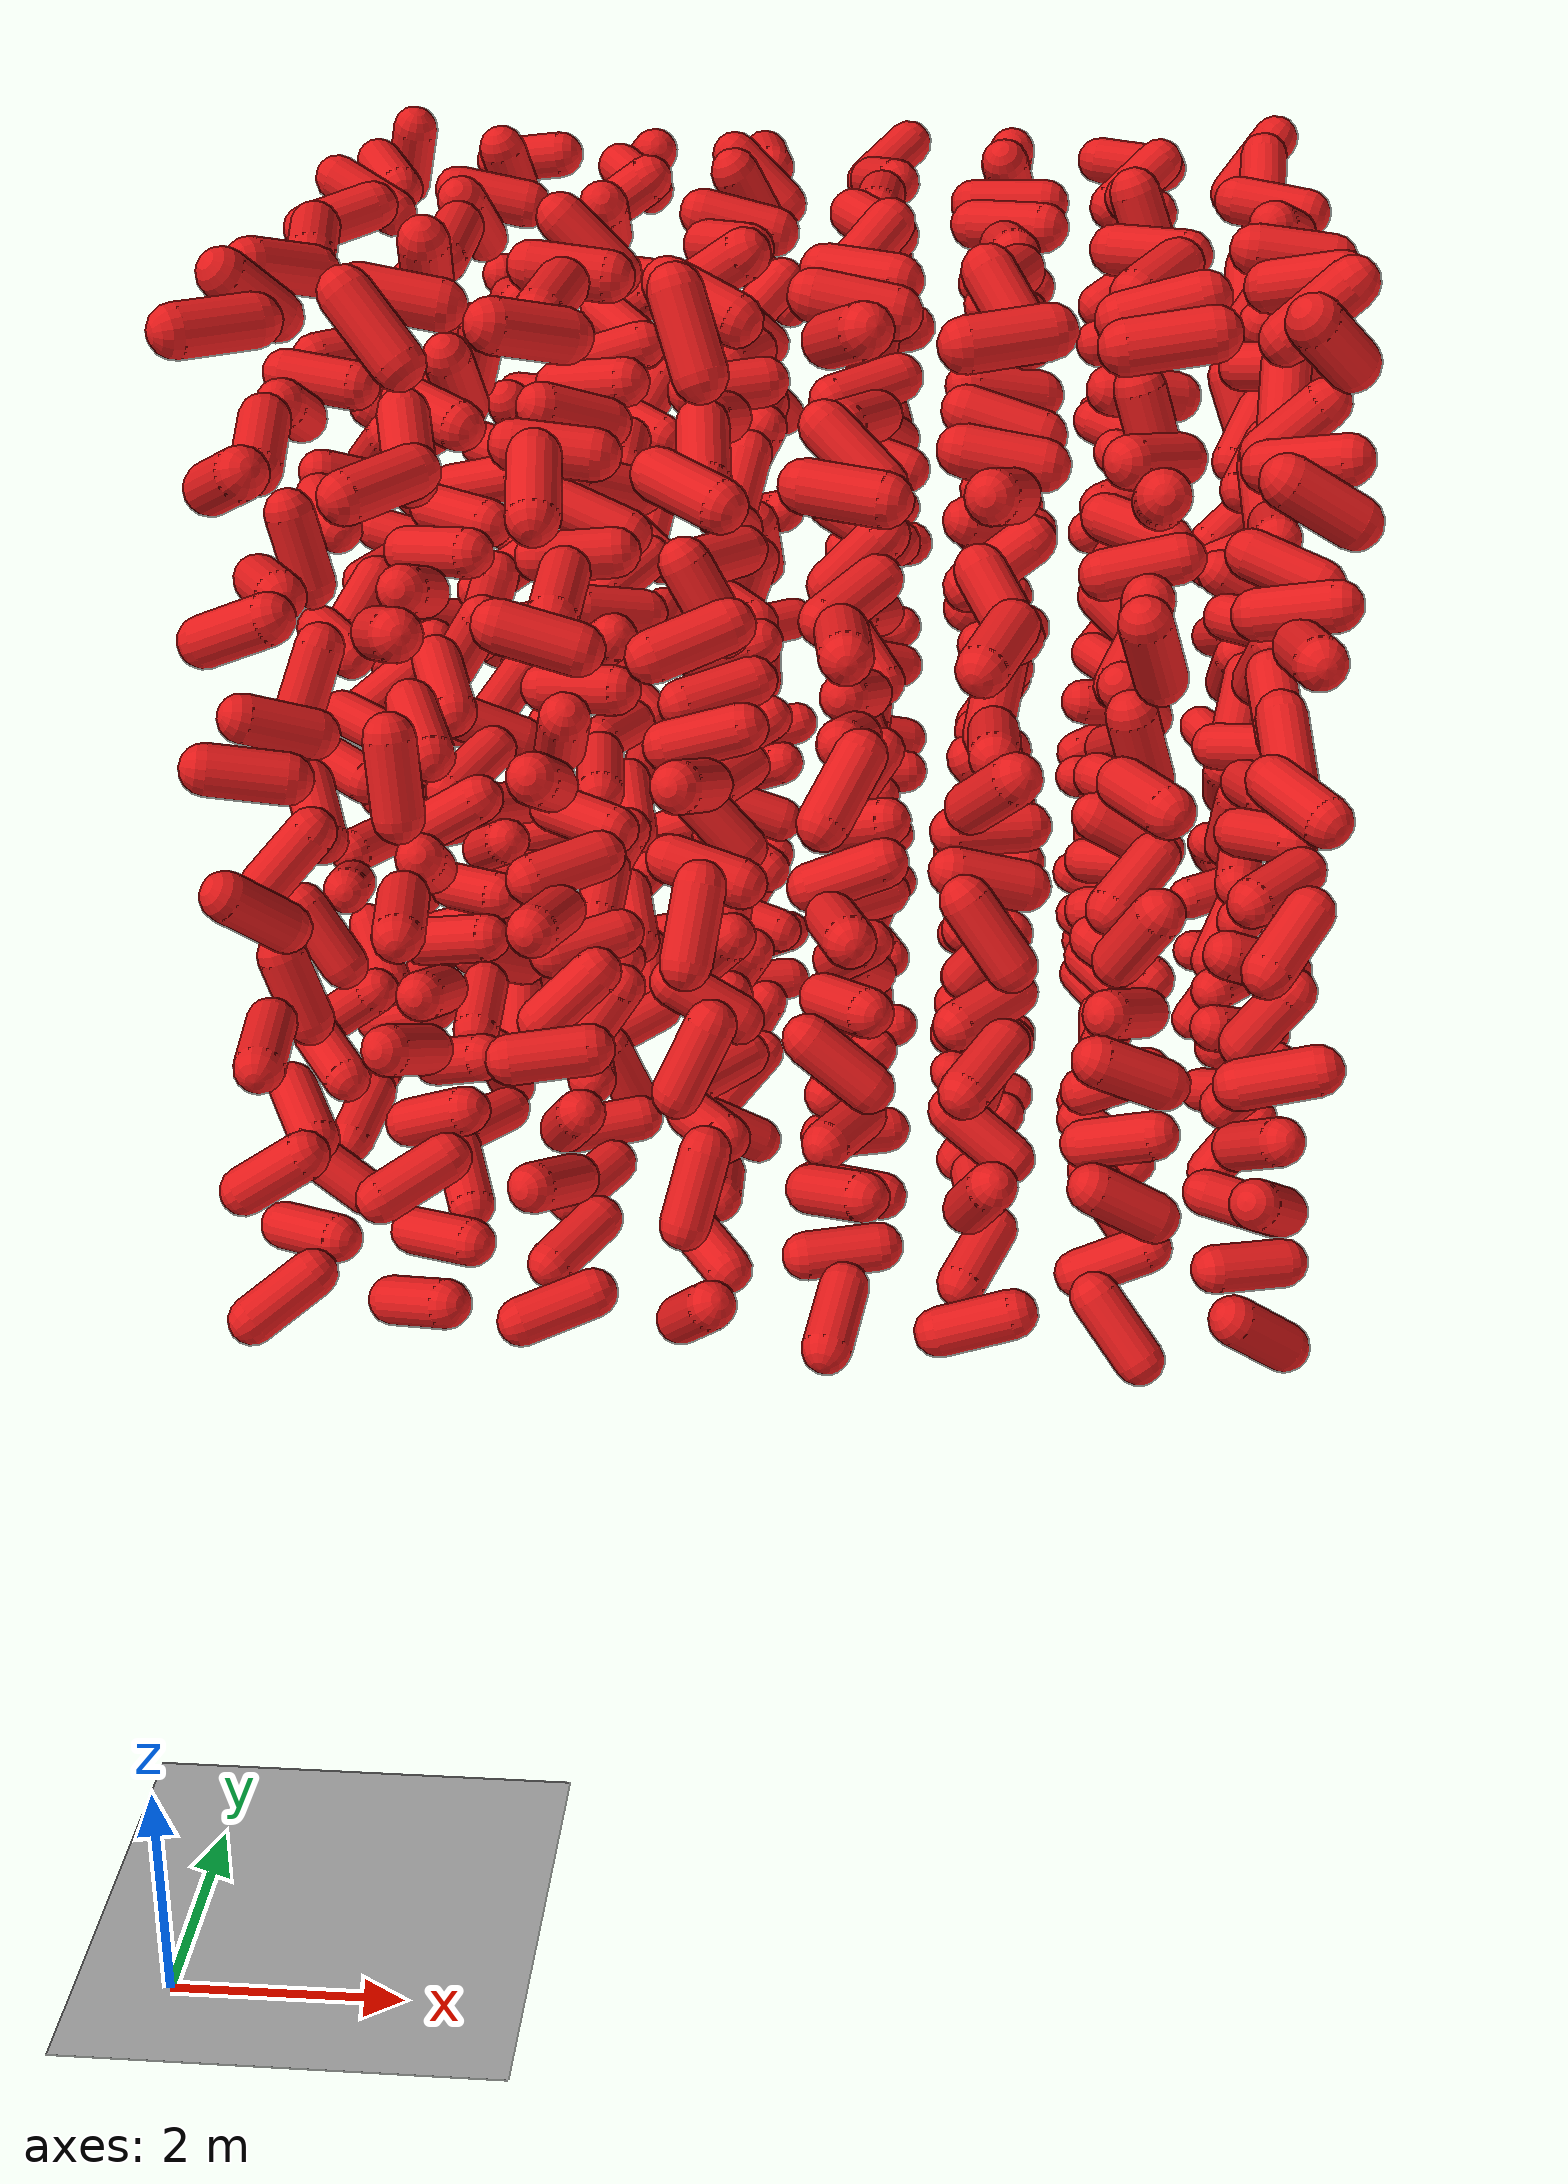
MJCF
<mujoco model="Humanoid and 100 objects">
    <compiler angle="degree"/>

    <option timestep="0.01" iterations="50" solver="PGS" jacobian="sparse" cone="elliptic" tolerance="1e-10"/>

    <size njmax="5000" nconmax="2000" nstack="1000000000"/>

    <default>
        <geom solimp=".9 .9 .01"/>

        <default class="object5">
			<geom type="capsule" material="geom" rgba=".9 .1 .1 1" size="0.200000 0.300000"/>
        </default>
    </default>

    <asset>
        <texture type="skybox" builtin="gradient" width="128" height="128" rgb1=".4 .6 .8" rgb2="0 0 0"/>
        <texture name="texgeom" type="cube" builtin="flat" mark="cross" width="128" height="128"
            rgb1="0.6 0.6 0.6" rgb2="0.6 0.6 0.6" markrgb="1 1 1"/>
        <texture name="texplane" type="2d" builtin="checker" rgb1=".4 .4 .4" rgb2=".6 .6 .6"
            width="512" height="512"/>
        <material name='geom' texture="texgeom" texuniform="true"/>
        <material name='MatPlane' reflectance='0.3' texture="texplane" texrepeat="1 1" texuniform="true"/>
    </asset>

    <visual>
        <quality shadowsize="4096" offsamples="8"/>
        <map znear="0.1" force="0.05"/>
    </visual>

    <statistic extent="4"/>

    <worldbody>
        <light directional="true" diffuse=".8 .8 .8" pos="0 0 10" dir="0 0 -10"/>

        <geom pos="0 0 0" type="plane" size="3 3 .5" rgba=".7 .7 .7 1" material="MatPlane"/>
		<body pos="1.100878 1.100946 6.100398" quat="-0.195774 0.523437 0.690892 -0.458644"> <freejoint/> <geom class="object5"/> </body>
		<body pos="1.100913 1.100986 7.200791" quat="0.835420 0.164048 0.439386 0.286535"> <freejoint/> <geom class="object5"/> </body>
		<body pos="1.100832 1.100905 8.300814" quat="0.607880 0.750868 -0.185290 0.179851"> <freejoint/> <geom class="object5"/> </body>
		<body pos="1.100208 1.100581 9.400184" quat="0.370693 0.429518 0.120193 -0.814650"> <freejoint/> <geom class="object5"/> </body>
		<body pos="1.100054 1.100472 10.500282" quat="0.541234 0.245686 0.726830 0.344125"> <freejoint/> <geom class="object5"/> </body>
		<body pos="1.100319 1.100975 11.600547" quat="0.064089 0.540098 -0.119821 0.830560"> <freejoint/> <geom class="object5"/> </body>
		<body pos="1.100159 1.100593 12.700567" quat="-0.455240 0.830419 0.040601 -0.318610"> <freejoint/> <geom class="object5"/> </body>
		<body pos="1.100268 1.100128 13.800566" quat="0.658670 -0.606368 0.352039 -0.273018"> <freejoint/> <geom class="object5"/> </body>
		<body pos="1.100057 2.200486 6.100982" quat="0.208257 0.650778 -0.165126 0.711232"> <freejoint/> <geom class="object5"/> </body>
		<body pos="1.100141 2.200557 7.200961" quat="0.829439 -0.469304 -0.298855 -0.049693"> <freejoint/> <geom class="object5"/> </body>
		<body pos="1.100349 2.200380 8.300307" quat="-0.805429 -0.112305 0.111773 0.571120"> <freejoint/> <geom class="object5"/> </body>
		<body pos="1.100514 2.200194 9.400419" quat="-0.055207 -0.345560 -0.102856 -0.931108"> <freejoint/> <geom class="object5"/> </body>
		<body pos="1.100798 2.200213 10.500157" quat="-0.555909 0.239491 -0.784824 -0.132895"> <freejoint/> <geom class="object5"/> </body>
		<body pos="1.100522 2.200053 11.600113" quat="-0.454109 0.162388 0.703268 0.522331"> <freejoint/> <geom class="object5"/> </body>
		<body pos="1.100304 2.200187 12.700913" quat="-0.459462 0.328939 -0.428892 -0.704801"> <freejoint/> <geom class="object5"/> </body>
		<body pos="1.100081 2.200435 13.800320" quat="-0.440038 0.717463 -0.539990 0.004860"> <freejoint/> <geom class="object5"/> </body>
		<body pos="1.100599 3.300446 6.100266" quat="-0.380216 -0.635713 -0.611949 -0.277171"> <freejoint/> <geom class="object5"/> </body>
		<body pos="1.100779 3.300520 7.200139" quat="0.396948 0.798518 -0.141631 0.429816"> <freejoint/> <geom class="object5"/> </body>
		<body pos="1.100864 3.300168 8.300619" quat="0.155601 -0.732375 0.618255 -0.239114"> <freejoint/> <geom class="object5"/> </body>
		<body pos="1.100855 3.300882 9.400553" quat="0.323333 0.811651 -0.346413 0.341579"> <freejoint/> <geom class="object5"/> </body>
		<body pos="1.100395 3.300700 10.500728" quat="-0.961524 0.180103 -0.120389 0.168939"> <freejoint/> <geom class="object5"/> </body>
		<body pos="1.100289 3.300791 11.600085" quat="0.252413 -0.095408 -0.071269 0.960263"> <freejoint/> <geom class="object5"/> </body>
		<body pos="1.100757 3.300052 12.700639" quat="0.395466 -0.567556 0.609094 0.387932"> <freejoint/> <geom class="object5"/> </body>
		<body pos="1.100227 3.300376 13.800860" quat="0.580808 -0.360154 0.695550 0.221722"> <freejoint/> <geom class="object5"/> </body>
		<body pos="1.100103 4.400737 6.100013" quat="0.788852 -0.492644 0.272861 0.246092"> <freejoint/> <geom class="object5"/> </body>
		<body pos="1.100624 4.400170 7.200976" quat="0.444088 -0.527429 -0.723453 0.034939"> <freejoint/> <geom class="object5"/> </body>
		<body pos="1.100911 4.400815 8.300680" quat="0.713310 0.515055 0.327080 -0.344856"> <freejoint/> <geom class="object5"/> </body>
		<body pos="1.100474 4.400055 9.400249" quat="0.361911 -0.625563 0.089318 0.685356"> <freejoint/> <geom class="object5"/> </body>
		<body pos="1.100944 4.400368 10.500161" quat="-0.748051 0.569341 0.330598 -0.083521"> <freejoint/> <geom class="object5"/> </body>
		<body pos="1.100574 4.400909 11.600904" quat="-0.627713 -0.681353 -0.375081 0.032376"> <freejoint/> <geom class="object5"/> </body>
		<body pos="1.100351 4.400619 12.700874" quat="-0.568803 0.539688 0.400448 -0.474176"> <freejoint/> <geom class="object5"/> </body>
		<body pos="1.100887 4.400509 13.800920" quat="-0.672670 0.486814 0.387659 0.400308"> <freejoint/> <geom class="object5"/> </body>
		<body pos="1.100037 5.500809 6.100332" quat="-0.712435 -0.659888 0.179584 -0.157269"> <freejoint/> <geom class="object5"/> </body>
		<body pos="1.100961 5.500983 7.200331" quat="-0.584651 0.373503 -0.139090 -0.706635"> <freejoint/> <geom class="object5"/> </body>
		<body pos="1.100835 5.500296 8.300420" quat="-0.695475 -0.674617 0.210071 0.130680"> <freejoint/> <geom class="object5"/> </body>
		<body pos="1.100178 5.500704 9.400216" quat="-0.476269 -0.211826 0.601659 0.605231"> <freejoint/> <geom class="object5"/> </body>
		<body pos="1.100405 5.500473 10.500463" quat="-0.756719 0.460354 0.058947 0.460408"> <freejoint/> <geom class="object5"/> </body>
		<body pos="1.100266 5.500278 11.600641" quat="0.668878 -0.031225 -0.586196 0.456073"> <freejoint/> <geom class="object5"/> </body>
		<body pos="1.100543 5.500443 12.700086" quat="0.194427 0.379577 0.578029 0.695702"> <freejoint/> <geom class="object5"/> </body>
		<body pos="1.100502 5.500316 13.800739" quat="-0.614238 -0.447075 0.649492 0.031553"> <freejoint/> <geom class="object5"/> </body>
		<body pos="1.100248 6.600419 6.100403" quat="-0.653084 0.314751 -0.516212 0.456003"> <freejoint/> <geom class="object5"/> </body>
		<body pos="1.100306 6.600778 7.200819" quat="-0.245821 0.297097 -0.689732 -0.612842"> <freejoint/> <geom class="object5"/> </body>
		<body pos="1.100606 6.600540 8.300569" quat="-0.575075 -0.634082 0.036487 -0.515653"> <freejoint/> <geom class="object5"/> </body>
		<body pos="1.100601 6.600069 9.400632" quat="-0.729110 -0.096257 -0.450148 -0.506458"> <freejoint/> <geom class="object5"/> </body>
		<body pos="1.100852 6.600590 10.500554" quat="-0.543936 0.632204 0.195119 0.516121"> <freejoint/> <geom class="object5"/> </body>
		<body pos="1.100168 6.600103 11.600535" quat="0.603563 0.067361 0.452407 -0.653071"> <freejoint/> <geom class="object5"/> </body>
		<body pos="1.100146 6.600929 12.700652" quat="0.752546 0.050184 -0.181454 0.631055"> <freejoint/> <geom class="object5"/> </body>
		<body pos="1.100290 6.600168 13.800466" quat="0.146616 -0.644137 0.534399 -0.527266"> <freejoint/> <geom class="object5"/> </body>
		<body pos="1.100448 7.700161 6.100845" quat="0.349802 -0.564686 -0.747258 0.019304"> <freejoint/> <geom class="object5"/> </body>
		<body pos="1.100482 7.700858 7.200307" quat="0.904543 0.060719 -0.012218 0.421859"> <freejoint/> <geom class="object5"/> </body>
		<body pos="1.100184 7.700886 8.300680" quat="-0.725958 0.312265 0.594092 0.150101"> <freejoint/> <geom class="object5"/> </body>
		<body pos="1.100569 7.700259 9.400880" quat="0.501495 -0.501818 -0.699133 0.088851"> <freejoint/> <geom class="object5"/> </body>
		<body pos="1.100831 7.700231 10.500092" quat="-0.316252 0.565989 -0.527027 0.549438"> <freejoint/> <geom class="object5"/> </body>
		<body pos="1.100402 7.700408 11.600739" quat="-0.468191 -0.474411 0.223232 0.711266"> <freejoint/> <geom class="object5"/> </body>
		<body pos="1.100238 7.700334 12.700594" quat="-0.657513 0.337065 -0.187884 0.647119"> <freejoint/> <geom class="object5"/> </body>
		<body pos="1.100627 7.700510 13.800680" quat="-0.598952 -0.619411 -0.495048 0.111861"> <freejoint/> <geom class="object5"/> </body>
		<body pos="1.100501 8.800162 6.100175" quat="-0.807466 -0.302086 -0.479694 -0.163205"> <freejoint/> <geom class="object5"/> </body>
		<body pos="1.100886 8.800371 7.200076" quat="0.290004 0.742738 -0.018428 -0.603240"> <freejoint/> <geom class="object5"/> </body>
		<body pos="1.100782 8.800348 8.300374" quat="-0.505664 -0.577847 -0.069966 0.636790"> <freejoint/> <geom class="object5"/> </body>
		<body pos="1.100384 8.800948 9.400953" quat="0.637419 -0.003083 -0.615722 0.463221"> <freejoint/> <geom class="object5"/> </body>
		<body pos="1.100002 8.800757 10.500263" quat="0.837647 -0.094749 -0.327778 0.426535"> <freejoint/> <geom class="object5"/> </body>
		<body pos="1.100863 8.800663 11.600626" quat="-0.058213 -0.733283 0.330552 -0.591306"> <freejoint/> <geom class="object5"/> </body>
		<body pos="1.100835 8.800539 12.700688" quat="0.880301 0.168267 0.269186 -0.352555"> <freejoint/> <geom class="object5"/> </body>
		<body pos="1.100349 8.800190 13.800782" quat="0.284960 -0.051140 0.236644 -0.927460"> <freejoint/> <geom class="object5"/> </body>
		<body pos="2.200816 1.100579 6.100960" quat="0.794533 0.346990 0.497337 0.031155"> <freejoint/> <geom class="object5"/> </body>
		<body pos="2.200935 1.100692 7.200726" quat="-0.507535 -0.110762 0.824168 -0.225580"> <freejoint/> <geom class="object5"/> </body>
		<body pos="2.200327 1.100880 8.300848" quat="0.193189 -0.079772 -0.557383 0.803517"> <freejoint/> <geom class="object5"/> </body>
		<body pos="2.200017 1.100184 9.400990" quat="0.423484 -0.420378 0.500141 0.627537"> <freejoint/> <geom class="object5"/> </body>
		<body pos="2.200108 1.100152 10.500544" quat="0.577174 -0.056086 0.006813 0.814664"> <freejoint/> <geom class="object5"/> </body>
		<body pos="2.200189 1.100275 11.600377" quat="-0.728290 -0.611269 -0.012700 -0.309488"> <freejoint/> <geom class="object5"/> </body>
		<body pos="2.200220 1.100033 12.700016" quat="-0.464792 -0.009046 0.761163 -0.452236"> <freejoint/> <geom class="object5"/> </body>
		<body pos="2.200801 1.100877 13.800317" quat="0.318599 0.687741 0.632139 0.160960"> <freejoint/> <geom class="object5"/> </body>
		<body pos="2.200117 2.200138 6.100349" quat="-0.657502 -0.008279 -0.668708 0.347062"> <freejoint/> <geom class="object5"/> </body>
		<body pos="2.200743 2.200423 7.200447" quat="0.202174 -0.431887 0.340373 -0.810398"> <freejoint/> <geom class="object5"/> </body>
		<body pos="2.200108 2.200241 8.300370" quat="-0.573607 -0.469354 -0.359536 0.566936"> <freejoint/> <geom class="object5"/> </body>
		<body pos="2.200738 2.200481 9.400601" quat="-0.795871 -0.463893 -0.209197 0.328068"> <freejoint/> <geom class="object5"/> </body>
		<body pos="2.200548 2.200946 10.500951" quat="0.291803 0.033443 -0.548297 -0.783009"> <freejoint/> <geom class="object5"/> </body>
		<body pos="2.200036 2.200885 11.600232" quat="-0.713374 -0.549111 -0.223362 0.373743"> <freejoint/> <geom class="object5"/> </body>
		<body pos="2.200826 2.200662 12.700710" quat="-0.413883 0.083833 0.410804 0.808030"> <freejoint/> <geom class="object5"/> </body>
		<body pos="2.200603 2.200418 13.800056" quat="0.720545 -0.210178 -0.604853 0.266069"> <freejoint/> <geom class="object5"/> </body>
		<body pos="2.200198 3.300258 6.100353" quat="-0.267488 -0.027846 0.503033 0.821360"> <freejoint/> <geom class="object5"/> </body>
		<body pos="2.200515 3.300935 7.200707" quat="-0.091663 -0.587444 0.574247 0.562803"> <freejoint/> <geom class="object5"/> </body>
		<body pos="2.200897 3.300721 8.300335" quat="0.751865 0.030985 0.626987 -0.201561"> <freejoint/> <geom class="object5"/> </body>
		<body pos="2.200863 3.300686 9.400493" quat="0.372661 -0.656987 -0.578347 0.308230"> <freejoint/> <geom class="object5"/> </body>
		<body pos="2.200719 3.300866 10.500324" quat="-0.001393 0.317874 -0.792778 0.520055"> <freejoint/> <geom class="object5"/> </body>
		<body pos="2.200809 3.300481 11.600358" quat="0.658819 -0.437089 -0.604996 0.094285"> <freejoint/> <geom class="object5"/> </body>
		<body pos="2.200167 3.300739 12.700955" quat="-0.636551 -0.493950 -0.591021 -0.038873"> <freejoint/> <geom class="object5"/> </body>
		<body pos="2.200202 3.300326 13.800151" quat="-0.080334 0.326989 -0.887816 -0.313701"> <freejoint/> <geom class="object5"/> </body>
		<body pos="2.200213 4.400876 6.100554" quat="0.538797 -0.202616 0.682077 0.451017"> <freejoint/> <geom class="object5"/> </body>
		<body pos="2.200861 4.400170 7.200307" quat="0.331924 0.471988 0.667821 -0.470180"> <freejoint/> <geom class="object5"/> </body>
		<body pos="2.200871 4.400771 8.300703" quat="-0.008146 -0.534790 0.401782 -0.743307"> <freejoint/> <geom class="object5"/> </body>
		<body pos="2.200272 4.400460 9.400099" quat="-0.403393 -0.044915 -0.559777 -0.722430"> <freejoint/> <geom class="object5"/> </body>
		<body pos="2.200634 4.400987 10.500831" quat="0.255554 -0.752559 -0.591662 0.135214"> <freejoint/> <geom class="object5"/> </body>
		<body pos="2.200039 4.400970 11.600210" quat="-0.091349 0.621477 -0.293126 -0.720763"> <freejoint/> <geom class="object5"/> </body>
		<body pos="2.200266 4.400314 12.700967" quat="0.142445 -0.549782 -0.766798 -0.299114"> <freejoint/> <geom class="object5"/> </body>
		<body pos="2.200335 4.400464 13.800553" quat="0.796854 -0.595658 0.087002 0.051443"> <freejoint/> <geom class="object5"/> </body>
		<body pos="2.200181 5.500186 6.100994" quat="0.652117 0.255742 0.109499 -0.705230"> <freejoint/> <geom class="object5"/> </body>
		<body pos="2.200623 5.500239 7.200544" quat="0.614135 0.550263 -0.063692 -0.562132"> <freejoint/> <geom class="object5"/> </body>
		<body pos="2.200419 5.500679 8.300345" quat="-0.581937 -0.109753 -0.519520 0.615957"> <freejoint/> <geom class="object5"/> </body>
		<body pos="2.200278 5.500694 9.400337" quat="0.538169 -0.199018 0.818322 0.033398"> <freejoint/> <geom class="object5"/> </body>
		<body pos="2.200711 5.500467 10.500448" quat="0.067813 -0.631989 -0.758110 0.145810"> <freejoint/> <geom class="object5"/> </body>
		<body pos="2.200756 5.500169 11.600208" quat="0.785423 0.092293 0.608619 -0.064620"> <freejoint/> <geom class="object5"/> </body>
		<body pos="2.200046 5.500553 12.700629" quat="0.255293 -0.598014 -0.753771 -0.095044"> <freejoint/> <geom class="object5"/> </body>
		<body pos="2.200403 5.500920 13.800030" quat="0.420108 0.276118 0.336029 -0.796463"> <freejoint/> <geom class="object5"/> </body>
		<body pos="2.200238 6.600880 6.100243" quat="0.661842 -0.206559 -0.244784 -0.677775"> <freejoint/> <geom class="object5"/> </body>
		<body pos="2.200504 6.600145 7.200350" quat="-0.869652 -0.428523 -0.065892 0.236074"> <freejoint/> <geom class="object5"/> </body>
		<body pos="2.200431 6.600914 8.300733" quat="0.653526 0.193803 -0.623664 0.382607"> <freejoint/> <geom class="object5"/> </body>
		<body pos="2.200092 6.600435 9.400982" quat="0.951904 0.014299 0.305582 -0.017158"> <freejoint/> <geom class="object5"/> </body>
		<body pos="2.200331 6.600002 10.500840" quat="-0.053503 0.869924 0.166970 -0.460967"> <freejoint/> <geom class="object5"/> </body>
		<body pos="2.200068 6.600081 11.600663" quat="0.624421 -0.680420 -0.167859 0.344892"> <freejoint/> <geom class="object5"/> </body>
		<body pos="2.200949 6.600715 12.700351" quat="-0.154357 -0.622290 -0.357315 -0.679157"> <freejoint/> <geom class="object5"/> </body>
		<body pos="2.200175 6.600343 13.800727" quat="-0.630899 0.106305 -0.765156 0.072116"> <freejoint/> <geom class="object5"/> </body>
		<body pos="2.200972 7.700061 6.100250" quat="-0.553247 -0.431174 0.636485 -0.320770"> <freejoint/> <geom class="object5"/> </body>
		<body pos="2.200222 7.700166 7.200312" quat="-0.379035 -0.466324 -0.587933 -0.541488"> <freejoint/> <geom class="object5"/> </body>
		<body pos="2.200382 7.700863 8.300704" quat="0.442644 -0.472106 -0.675131 -0.354092"> <freejoint/> <geom class="object5"/> </body>
		<body pos="2.200834 7.700471 9.400204" quat="0.148117 0.619560 0.532853 0.557023"> <freejoint/> <geom class="object5"/> </body>
		<body pos="2.200752 7.700449 10.500222" quat="0.591403 0.680841 0.375140 0.214400"> <freejoint/> <geom class="object5"/> </body>
		<body pos="2.200739 7.700471 11.600526" quat="-0.324497 0.936525 -0.075676 0.109065"> <freejoint/> <geom class="object5"/> </body>
		<body pos="2.200007 7.700305 12.700549" quat="-0.346274 0.179578 0.722051 0.571392"> <freejoint/> <geom class="object5"/> </body>
		<body pos="2.200875 7.700754 13.800693" quat="0.616281 0.070166 -0.249079 0.743797"> <freejoint/> <geom class="object5"/> </body>
		<body pos="2.200340 8.800101 6.101000" quat="0.334699 0.030566 -0.667504 0.664440"> <freejoint/> <geom class="object5"/> </body>
		<body pos="2.200467 8.800549 7.200035" quat="-0.737533 -0.094550 -0.631205 -0.220649"> <freejoint/> <geom class="object5"/> </body>
		<body pos="2.200208 8.800351 8.300864" quat="0.342026 0.382178 -0.844451 0.154472"> <freejoint/> <geom class="object5"/> </body>
		<body pos="2.200554 8.800961 9.400918" quat="0.480949 -0.486208 0.383013 -0.620960"> <freejoint/> <geom class="object5"/> </body>
		<body pos="2.200363 8.800088 10.500214" quat="-0.466761 -0.459115 0.204364 -0.727724"> <freejoint/> <geom class="object5"/> </body>
		<body pos="2.200087 8.800199 11.600750" quat="0.446362 -0.079397 0.664599 -0.593941"> <freejoint/> <geom class="object5"/> </body>
		<body pos="2.200949 8.800020 12.700128" quat="0.204323 0.489382 0.595855 0.603088"> <freejoint/> <geom class="object5"/> </body>
		<body pos="2.200548 8.800114 13.800799" quat="0.529022 0.531296 0.393033 0.532340"> <freejoint/> <geom class="object5"/> </body>
		<body pos="3.300004 1.100812 6.100050" quat="0.633065 -0.496278 0.326746 -0.496159"> <freejoint/> <geom class="object5"/> </body>
		<body pos="3.300063 1.100385 7.200458" quat="-0.758607 -0.426210 0.416882 -0.262813"> <freejoint/> <geom class="object5"/> </body>
		<body pos="3.300386 1.100093 8.300962" quat="0.266476 0.587329 0.307927 0.699440"> <freejoint/> <geom class="object5"/> </body>
		<body pos="3.300888 1.100301 9.400717" quat="-0.349323 -0.425679 -0.511662 0.659525"> <freejoint/> <geom class="object5"/> </body>
		<body pos="3.300531 1.100422 10.500414" quat="0.730451 0.496187 0.220032 -0.414519"> <freejoint/> <geom class="object5"/> </body>
		<body pos="3.300161 1.100084 11.600158" quat="0.378150 -0.634323 0.487566 -0.465742"> <freejoint/> <geom class="object5"/> </body>
		<body pos="3.300356 1.100004 12.700870" quat="-0.640458 0.385818 -0.290644 -0.597063"> <freejoint/> <geom class="object5"/> </body>
		<body pos="3.300230 1.100640 13.800226" quat="-0.574146 -0.612689 0.098858 0.534037"> <freejoint/> <geom class="object5"/> </body>
		<body pos="3.300126 2.200729 6.100189" quat="-0.590558 -0.598388 0.537357 -0.066487"> <freejoint/> <geom class="object5"/> </body>
		<body pos="3.300868 2.200302 7.200266" quat="-0.436935 0.697306 0.557482 0.109842"> <freejoint/> <geom class="object5"/> </body>
		<body pos="3.300035 2.200518 8.300981" quat="0.329084 0.663499 -0.631328 -0.229994"> <freejoint/> <geom class="object5"/> </body>
		<body pos="3.300079 2.200935 9.400977" quat="0.558639 0.113457 0.640759 0.514274"> <freejoint/> <geom class="object5"/> </body>
		<body pos="3.300303 2.200275 10.500176" quat="0.391282 -0.771211 -0.484524 -0.131792"> <freejoint/> <geom class="object5"/> </body>
		<body pos="3.300593 2.200100 11.600740" quat="-0.499374 0.377060 0.446109 0.639873"> <freejoint/> <geom class="object5"/> </body>
		<body pos="3.300274 2.200994 12.700974" quat="0.571201 0.420431 0.607892 0.356980"> <freejoint/> <geom class="object5"/> </body>
		<body pos="3.300955 2.200152 13.800158" quat="0.559752 -0.388707 0.506627 0.528123"> <freejoint/> <geom class="object5"/> </body>
		<body pos="3.300035 3.300372 6.100037" quat="-0.409126 -0.103864 0.755888 -0.500462"> <freejoint/> <geom class="object5"/> </body>
		<body pos="3.300760 3.300535 7.200604" quat="-0.505847 0.381541 0.578562 0.513626"> <freejoint/> <geom class="object5"/> </body>
		<body pos="3.300302 3.300328 8.300155" quat="-0.609916 -0.576087 0.491644 0.233264"> <freejoint/> <geom class="object5"/> </body>
		<body pos="3.300722 3.300640 9.400462" quat="-0.513167 -0.688957 -0.299488 -0.415096"> <freejoint/> <geom class="object5"/> </body>
		<body pos="3.300205 3.300433 10.500784" quat="-0.251030 -0.597664 0.415561 0.638036"> <freejoint/> <geom class="object5"/> </body>
		<body pos="3.300984 3.300811 11.600550" quat="-0.553354 -0.436347 -0.516984 -0.485930"> <freejoint/> <geom class="object5"/> </body>
		<body pos="3.300168 3.300666 12.700840" quat="0.374121 0.178936 0.793481 0.445425"> <freejoint/> <geom class="object5"/> </body>
		<body pos="3.300288 3.300493 13.800312" quat="-0.472005 0.587475 0.336587 -0.564618"> <freejoint/> <geom class="object5"/> </body>
		<body pos="3.300445 4.400794 6.100912" quat="0.568756 -0.567091 0.363858 -0.471732"> <freejoint/> <geom class="object5"/> </body>
		<body pos="3.300976 4.400895 7.200034" quat="0.564078 0.258493 0.115698 0.775636"> <freejoint/> <geom class="object5"/> </body>
		<body pos="3.300534 4.400686 8.300954" quat="0.514718 -0.361397 -0.421097 -0.653556"> <freejoint/> <geom class="object5"/> </body>
		<body pos="3.300578 4.400808 9.400629" quat="-0.128146 -0.249918 0.737838 -0.613770"> <freejoint/> <geom class="object5"/> </body>
		<body pos="3.300324 4.400202 10.500844" quat="-0.045309 0.600076 -0.635497 -0.483735"> <freejoint/> <geom class="object5"/> </body>
		<body pos="3.300914 4.400193 11.600438" quat="-0.353172 0.527303 -0.629437 0.448364"> <freejoint/> <geom class="object5"/> </body>
		<body pos="3.300218 4.400631 12.700551" quat="-0.652587 0.246210 0.716351 0.018752"> <freejoint/> <geom class="object5"/> </body>
		<body pos="3.300459 4.400165 13.800688" quat="-0.375591 0.226320 -0.893106 0.100362"> <freejoint/> <geom class="object5"/> </body>
		<body pos="3.300184 5.500345 6.100983" quat="-0.206845 0.425656 -0.880831 0.013000"> <freejoint/> <geom class="object5"/> </body>
		<body pos="3.300755 5.500274 7.200187" quat="0.651019 0.466898 -0.238257 0.549012"> <freejoint/> <geom class="object5"/> </body>
		<body pos="3.300738 5.500141 8.300217" quat="-0.331220 0.701119 0.630876 0.026855"> <freejoint/> <geom class="object5"/> </body>
		<body pos="3.300878 5.500217 9.400922" quat="0.700980 -0.660837 0.268175 0.002170"> <freejoint/> <geom class="object5"/> </body>
		<body pos="3.300903 5.500798 10.500156" quat="-0.670069 -0.550669 0.310814 0.388801"> <freejoint/> <geom class="object5"/> </body>
		<body pos="3.300380 5.500545 11.600310" quat="-0.184630 0.783954 0.203154 0.556827"> <freejoint/> <geom class="object5"/> </body>
		<body pos="3.300559 5.500285 12.700811" quat="-0.469531 0.509847 -0.308458 0.651499"> <freejoint/> <geom class="object5"/> </body>
		<body pos="3.300631 5.500204 13.800534" quat="0.478898 0.241782 0.411358 -0.736873"> <freejoint/> <geom class="object5"/> </body>
		<body pos="3.300231 6.600039 6.100103" quat="-0.167753 -0.713798 -0.320717 0.599577"> <freejoint/> <geom class="object5"/> </body>
		<body pos="3.300600 6.600057 7.200699" quat="-0.686531 0.263243 0.377678 0.562794"> <freejoint/> <geom class="object5"/> </body>
		<body pos="3.300647 6.600947 8.300878" quat="0.706247 -0.295877 -0.359180 -0.533537"> <freejoint/> <geom class="object5"/> </body>
		<body pos="3.300206 6.600756 9.400952" quat="-0.132447 0.640733 -0.636482 0.408424"> <freejoint/> <geom class="object5"/> </body>
		<body pos="3.300281 6.600372 10.500984" quat="0.366498 0.796607 0.186624 -0.443021"> <freejoint/> <geom class="object5"/> </body>
		<body pos="3.300232 6.600360 11.600088" quat="-0.756996 0.628042 -0.104837 -0.146730"> <freejoint/> <geom class="object5"/> </body>
		<body pos="3.300017 6.600398 12.700696" quat="0.536168 0.352133 0.746404 -0.177223"> <freejoint/> <geom class="object5"/> </body>
		<body pos="3.300487 6.600913 13.800572" quat="0.594593 0.388215 0.247118 0.659303"> <freejoint/> <geom class="object5"/> </body>
		<body pos="3.300781 7.700217 6.100961" quat="-0.841291 0.231195 0.157148 0.462690"> <freejoint/> <geom class="object5"/> </body>
		<body pos="3.300736 7.700358 7.200468" quat="0.814184 -0.123025 0.344359 -0.450984"> <freejoint/> <geom class="object5"/> </body>
		<body pos="3.300080 7.700022 8.300995" quat="-0.134802 0.472284 0.870060 -0.042099"> <freejoint/> <geom class="object5"/> </body>
		<body pos="3.300836 7.700344 9.400493" quat="-0.774287 -0.490628 -0.391405 0.081025"> <freejoint/> <geom class="object5"/> </body>
		<body pos="3.300952 7.700181 10.500158" quat="0.047963 0.739156 -0.441903 0.506033"> <freejoint/> <geom class="object5"/> </body>
		<body pos="3.300451 7.700714 11.600505" quat="0.307529 0.787319 -0.058219 0.531193"> <freejoint/> <geom class="object5"/> </body>
		<body pos="3.300191 7.700300 12.700270" quat="-0.030500 0.637764 -0.571700 -0.515254"> <freejoint/> <geom class="object5"/> </body>
		<body pos="3.300319 7.700758 13.800653" quat="-0.138010 -0.556947 0.544967 -0.611370"> <freejoint/> <geom class="object5"/> </body>
		<body pos="3.300725 8.800078 6.100275" quat="0.538701 0.407071 0.478567 0.561309"> <freejoint/> <geom class="object5"/> </body>
		<body pos="3.300652 8.800282 7.200451" quat="-0.819010 0.094426 -0.563289 0.054881"> <freejoint/> <geom class="object5"/> </body>
		<body pos="3.300857 8.800462 8.300190" quat="-0.631642 -0.135346 -0.424901 0.634168"> <freejoint/> <geom class="object5"/> </body>
		<body pos="3.300055 8.800504 9.400748" quat="-0.405789 0.220059 -0.594582 -0.658317"> <freejoint/> <geom class="object5"/> </body>
		<body pos="3.300068 8.800346 10.500987" quat="-0.915640 0.347420 -0.024293 0.200778"> <freejoint/> <geom class="object5"/> </body>
		<body pos="3.300607 8.800285 11.600197" quat="-0.250356 -0.291027 0.919829 0.080868"> <freejoint/> <geom class="object5"/> </body>
		<body pos="3.300187 8.800447 12.700279" quat="0.547540 0.603411 0.392229 0.426910"> <freejoint/> <geom class="object5"/> </body>
		<body pos="3.300234 8.800578 13.800520" quat="0.826553 0.518047 0.213083 -0.055073"> <freejoint/> <geom class="object5"/> </body>
		<body pos="4.400373 1.100877 6.100187" quat="-0.167183 -0.199788 0.871522 0.415432"> <freejoint/> <geom class="object5"/> </body>
		<body pos="4.400360 1.100405 7.200334" quat="-0.121320 0.144415 0.157675 0.969311"> <freejoint/> <geom class="object5"/> </body>
		<body pos="4.400678 1.100243 8.300962" quat="0.173755 0.805108 -0.548582 -0.143761"> <freejoint/> <geom class="object5"/> </body>
		<body pos="4.400928 1.100616 9.400860" quat="-0.481208 0.179389 0.168094 0.841429"> <freejoint/> <geom class="object5"/> </body>
		<body pos="4.400607 1.100505 10.500109" quat="0.005310 0.165553 0.572060 -0.803313"> <freejoint/> <geom class="object5"/> </body>
		<body pos="4.400788 1.100694 11.600778" quat="-0.568713 -0.096445 0.803910 -0.144888"> <freejoint/> <geom class="object5"/> </body>
		<body pos="4.400062 1.100764 12.700939" quat="-0.616590 -0.570550 -0.530297 -0.114345"> <freejoint/> <geom class="object5"/> </body>
		<body pos="4.400434 1.100172 13.800567" quat="0.681859 -0.216278 -0.005103 0.698761"> <freejoint/> <geom class="object5"/> </body>
		<body pos="4.400980 2.200220 6.100878" quat="-0.448990 -0.040463 0.598994 0.661798"> <freejoint/> <geom class="object5"/> </body>
		<body pos="4.400657 2.200882 7.200718" quat="-0.354320 0.650353 -0.319864 -0.590919"> <freejoint/> <geom class="object5"/> </body>
		<body pos="4.400366 2.200327 8.300320" quat="-0.332259 -0.601960 -0.633772 -0.354372"> <freejoint/> <geom class="object5"/> </body>
		<body pos="4.400730 2.200729 9.400817" quat="0.294815 0.759791 0.156277 0.558013"> <freejoint/> <geom class="object5"/> </body>
		<body pos="4.400641 2.200892 10.500761" quat="0.691637 -0.268293 0.534162 -0.405373"> <freejoint/> <geom class="object5"/> </body>
		<body pos="4.400742 2.200183 11.600258" quat="-0.698987 -0.171128 0.185751 0.669051"> <freejoint/> <geom class="object5"/> </body>
		<body pos="4.400065 2.200742 12.700551" quat="-0.086804 -0.054530 -0.863701 0.493470"> <freejoint/> <geom class="object5"/> </body>
		<body pos="4.400611 2.200981 13.800080" quat="0.184001 0.445512 -0.359058 -0.799212"> <freejoint/> <geom class="object5"/> </body>
		<body pos="4.400119 3.300055 6.100749" quat="0.543972 -0.579465 -0.456048 -0.400419"> <freejoint/> <geom class="object5"/> </body>
		<body pos="4.400863 3.300366 7.200556" quat="0.532033 0.153358 -0.721527 0.415718"> <freejoint/> <geom class="object5"/> </body>
		<body pos="4.400733 3.300615 8.300038" quat="-0.367842 -0.358879 0.256784 -0.818511"> <freejoint/> <geom class="object5"/> </body>
		<body pos="4.400634 3.300218 9.400070" quat="0.245005 0.588078 0.728898 0.250690"> <freejoint/> <geom class="object5"/> </body>
		<body pos="4.400933 3.300552 10.500691" quat="-0.036325 -0.727456 -0.276642 0.626863"> <freejoint/> <geom class="object5"/> </body>
		<body pos="4.400237 3.300773 11.600076" quat="-0.417728 -0.671635 -0.209122 0.575045"> <freejoint/> <geom class="object5"/> </body>
		<body pos="4.400261 3.300087 12.700037" quat="-0.221539 0.387812 0.667437 0.595860"> <freejoint/> <geom class="object5"/> </body>
		<body pos="4.400028 3.300638 13.800936" quat="0.029151 -0.814306 0.332728 0.474708"> <freejoint/> <geom class="object5"/> </body>
		<body pos="4.400977 4.400797 6.100413" quat="0.483628 -0.235324 0.840176 0.069508"> <freejoint/> <geom class="object5"/> </body>
		<body pos="4.400353 4.400761 7.200982" quat="-0.181145 0.731410 -0.639624 -0.152014"> <freejoint/> <geom class="object5"/> </body>
		<body pos="4.400175 4.400483 8.300081" quat="-0.856424 0.112479 -0.147584 -0.481773"> <freejoint/> <geom class="object5"/> </body>
		<body pos="4.400064 4.400014 9.400781" quat="0.491384 -0.650902 -0.271529 -0.511018"> <freejoint/> <geom class="object5"/> </body>
		<body pos="4.400899 4.400409 10.500647" quat="0.392447 -0.779535 -0.287621 0.394441"> <freejoint/> <geom class="object5"/> </body>
		<body pos="4.400459 4.400607 11.600210" quat="0.144266 -0.394939 -0.750381 -0.510038"> <freejoint/> <geom class="object5"/> </body>
		<body pos="4.400045 4.400118 12.700015" quat="-0.340379 0.483489 0.551149 -0.588740"> <freejoint/> <geom class="object5"/> </body>
		<body pos="4.400834 4.400501 13.800469" quat="-0.629725 -0.670771 -0.060671 -0.387081"> <freejoint/> <geom class="object5"/> </body>
		<body pos="4.400574 5.500962 6.100937" quat="0.477721 0.621297 -0.621106 -0.000489"> <freejoint/> <geom class="object5"/> </body>
		<body pos="4.400778 5.500750 7.200057" quat="0.356945 -0.775649 -0.520536 0.000844"> <freejoint/> <geom class="object5"/> </body>
		<body pos="4.400114 5.500527 8.300264" quat="0.461968 -0.097897 0.822602 -0.316746"> <freejoint/> <geom class="object5"/> </body>
		<body pos="4.400200 5.500888 9.400729" quat="0.448611 0.251614 -0.840005 -0.172715"> <freejoint/> <geom class="object5"/> </body>
		<body pos="4.400116 5.500144 10.500131" quat="0.712908 -0.578982 -0.390680 -0.062539"> <freejoint/> <geom class="object5"/> </body>
		<body pos="4.400814 5.500324 11.600782" quat="0.070099 0.610984 0.743257 -0.263351"> <freejoint/> <geom class="object5"/> </body>
		<body pos="4.400542 5.500862 12.700091" quat="-0.593664 0.679891 0.190345 0.386109"> <freejoint/> <geom class="object5"/> </body>
		<body pos="4.400343 5.500497 13.800396" quat="0.590086 -0.202387 0.757404 -0.192816"> <freejoint/> <geom class="object5"/> </body>
		<body pos="4.400601 6.600311 6.100263" quat="0.932307 0.048425 0.246771 0.259928"> <freejoint/> <geom class="object5"/> </body>
		<body pos="4.400858 6.600506 7.200727" quat="0.561212 0.545263 0.553809 0.284650"> <freejoint/> <geom class="object5"/> </body>
		<body pos="4.400978 6.600683 8.300521" quat="0.478901 0.496948 -0.279947 -0.667328"> <freejoint/> <geom class="object5"/> </body>
		<body pos="4.400564 6.600220 9.400344" quat="-0.617671 -0.588165 -0.377365 0.360750"> <freejoint/> <geom class="object5"/> </body>
		<body pos="4.400644 6.600093 10.500212" quat="0.055209 0.194972 -0.914536 -0.350089"> <freejoint/> <geom class="object5"/> </body>
		<body pos="4.400280 6.600798 11.600612" quat="-0.007496 -0.223067 0.098468 -0.969788"> <freejoint/> <geom class="object5"/> </body>
		<body pos="4.400517 6.600142 12.700398" quat="-0.326280 -0.376998 -0.290276 0.816795"> <freejoint/> <geom class="object5"/> </body>
		<body pos="4.400551 6.600881 13.800361" quat="-0.252581 0.900689 -0.327631 0.132737"> <freejoint/> <geom class="object5"/> </body>
		<body pos="4.400181 7.700337 6.100418" quat="0.128466 -0.598609 -0.356701 0.705641"> <freejoint/> <geom class="object5"/> </body>
		<body pos="4.400768 7.700065 7.200994" quat="0.172392 0.637296 0.582406 -0.474276"> <freejoint/> <geom class="object5"/> </body>
		<body pos="4.400720 7.700975 8.300101" quat="-0.168006 -0.504720 0.200922 -0.822595"> <freejoint/> <geom class="object5"/> </body>
		<body pos="4.400075 7.700921 9.400654" quat="0.211835 0.297241 0.822627 -0.435956"> <freejoint/> <geom class="object5"/> </body>
		<body pos="4.400343 7.700657 10.500071" quat="-0.615572 -0.212082 -0.195128 0.733496"> <freejoint/> <geom class="object5"/> </body>
		<body pos="4.400200 7.700819 11.600598" quat="0.147376 -0.178420 -0.459222 -0.857649"> <freejoint/> <geom class="object5"/> </body>
		<body pos="4.400564 7.700750 12.700448" quat="0.713457 -0.345316 0.182638 -0.581704"> <freejoint/> <geom class="object5"/> </body>
		<body pos="4.400047 7.700021 13.800277" quat="-0.231480 0.703127 -0.594217 0.314541"> <freejoint/> <geom class="object5"/> </body>
		<body pos="4.400787 8.800159 6.100684" quat="-0.515376 0.494139 0.698701 -0.045067"> <freejoint/> <geom class="object5"/> </body>
		<body pos="4.400576 8.800171 7.200351" quat="-0.121111 0.183682 0.875661 0.429896"> <freejoint/> <geom class="object5"/> </body>
		<body pos="4.400748 8.800664 8.300009" quat="0.075046 -0.591835 -0.012315 -0.802463"> <freejoint/> <geom class="object5"/> </body>
		<body pos="4.400150 8.800920 9.400456" quat="-0.029575 -0.597217 -0.403783 0.692399"> <freejoint/> <geom class="object5"/> </body>
		<body pos="4.400775 8.800497 10.500346" quat="0.582670 -0.601062 -0.542371 -0.071094"> <freejoint/> <geom class="object5"/> </body>
		<body pos="4.400963 8.800955 11.600870" quat="-0.438076 0.729944 -0.524432 -0.015554"> <freejoint/> <geom class="object5"/> </body>
		<body pos="4.400053 8.800389 12.700887" quat="0.352694 0.712723 0.567737 0.212856"> <freejoint/> <geom class="object5"/> </body>
		<body pos="4.400823 8.800436 13.800897" quat="-0.360447 0.426790 -0.523419 -0.643398"> <freejoint/> <geom class="object5"/> </body>
		<body pos="5.500164 1.100538 6.100744" quat="-0.611702 0.441676 0.283159 0.592084"> <freejoint/> <geom class="object5"/> </body>
		<body pos="5.500943 1.100109 7.200737" quat="0.201822 -0.326291 0.517620 -0.764769"> <freejoint/> <geom class="object5"/> </body>
		<body pos="5.500321 1.100026 8.300471" quat="0.335139 -0.546822 0.719789 -0.265653"> <freejoint/> <geom class="object5"/> </body>
		<body pos="5.500665 1.100633 9.400135" quat="-0.410318 -0.522178 0.434700 -0.608280"> <freejoint/> <geom class="object5"/> </body>
		<body pos="5.500038 1.100796 10.500007" quat="-0.837836 0.389168 -0.074772 0.375484"> <freejoint/> <geom class="object5"/> </body>
		<body pos="5.500108 1.100868 11.600816" quat="0.230524 0.160333 0.696466 -0.660368"> <freejoint/> <geom class="object5"/> </body>
		<body pos="5.500782 1.100671 12.700903" quat="0.345789 -0.670779 -0.127092 0.643687"> <freejoint/> <geom class="object5"/> </body>
		<body pos="5.500148 1.100091 13.800508" quat="-0.082606 0.468757 -0.654416 -0.587522"> <freejoint/> <geom class="object5"/> </body>
		<body pos="5.500988 2.200036 6.100227" quat="0.613123 0.438908 -0.587974 -0.292793"> <freejoint/> <geom class="object5"/> </body>
		<body pos="5.500734 2.200926 7.200985" quat="-0.502423 0.239476 -0.665085 -0.497880"> <freejoint/> <geom class="object5"/> </body>
		<body pos="5.500337 2.200750 8.300181" quat="0.329386 -0.704805 0.268648 0.567964"> <freejoint/> <geom class="object5"/> </body>
		<body pos="5.500246 2.200089 9.400835" quat="0.072897 -0.832545 -0.049796 0.546878"> <freejoint/> <geom class="object5"/> </body>
		<body pos="5.500055 2.200552 10.500421" quat="-0.445642 0.631423 0.460935 0.436173"> <freejoint/> <geom class="object5"/> </body>
		<body pos="5.500847 2.200800 11.600466" quat="-0.010680 -0.542823 -0.609989 0.577185"> <freejoint/> <geom class="object5"/> </body>
		<body pos="5.500480 2.200922 12.700125" quat="0.213834 -0.518431 0.737125 -0.377029"> <freejoint/> <geom class="object5"/> </body>
		<body pos="5.500852 2.200784 13.800898" quat="0.486295 -0.437260 0.627886 -0.421995"> <freejoint/> <geom class="object5"/> </body>
		<body pos="5.500493 3.300099 6.100090" quat="-0.715960 0.130517 0.684071 0.049131"> <freejoint/> <geom class="object5"/> </body>
		<body pos="5.500345 3.300267 7.200545" quat="-0.648094 0.124367 -0.550855 -0.510946"> <freejoint/> <geom class="object5"/> </body>
		<body pos="5.500156 3.300001 8.300150" quat="0.558997 0.045093 0.472545 -0.679846"> <freejoint/> <geom class="object5"/> </body>
		<body pos="5.500843 3.300315 9.400753" quat="-0.179078 -0.598961 0.529342 0.573563"> <freejoint/> <geom class="object5"/> </body>
		<body pos="5.500642 3.300400 10.500811" quat="-0.484894 0.471900 -0.632677 -0.376707"> <freejoint/> <geom class="object5"/> </body>
		<body pos="5.500577 3.300469 11.600926" quat="0.065567 -0.363586 0.087766 -0.925097"> <freejoint/> <geom class="object5"/> </body>
		<body pos="5.500634 3.300686 12.700429" quat="-0.319054 -0.029989 0.679713 -0.659770"> <freejoint/> <geom class="object5"/> </body>
		<body pos="5.500511 3.300105 13.800905" quat="0.624203 -0.554896 -0.410953 0.365483"> <freejoint/> <geom class="object5"/> </body>
		<body pos="5.500203 4.400584 6.100120" quat="-0.216993 -0.539213 -0.488735 -0.650616"> <freejoint/> <geom class="object5"/> </body>
		<body pos="5.500290 4.400630 7.200806" quat="-0.392465 0.640927 -0.481232 -0.451219"> <freejoint/> <geom class="object5"/> </body>
		<body pos="5.500444 4.400366 8.300623" quat="-0.607554 0.093493 -0.688638 -0.384596"> <freejoint/> <geom class="object5"/> </body>
		<body pos="5.500426 4.400793 9.400359" quat="-0.715243 0.252426 -0.163418 0.630875"> <freejoint/> <geom class="object5"/> </body>
		<body pos="5.500505 4.400837 10.500027" quat="0.715413 -0.432635 -0.047277 0.546604"> <freejoint/> <geom class="object5"/> </body>
		<body pos="5.500807 4.400918 11.600006" quat="0.702473 0.221308 -0.462531 -0.493578"> <freejoint/> <geom class="object5"/> </body>
		<body pos="5.500678 4.400150 12.700342" quat="0.757296 -0.225140 0.594164 0.150941"> <freejoint/> <geom class="object5"/> </body>
		<body pos="5.500637 4.400310 13.800139" quat="0.385779 0.877910 -0.069647 -0.274952"> <freejoint/> <geom class="object5"/> </body>
		<body pos="5.500207 5.500223 6.100244" quat="0.379891 0.552375 -0.470243 0.573965"> <freejoint/> <geom class="object5"/> </body>
		<body pos="5.500322 5.500111 7.200276" quat="-0.387676 0.419169 -0.754221 -0.324276"> <freejoint/> <geom class="object5"/> </body>
		<body pos="5.500861 5.500523 8.300371" quat="-0.440724 0.181381 0.280493 -0.833179"> <freejoint/> <geom class="object5"/> </body>
		<body pos="5.500143 5.501000 9.400128" quat="-0.003088 0.139005 -0.616751 -0.774782"> <freejoint/> <geom class="object5"/> </body>
		<body pos="5.500950 5.500631 10.500652" quat="0.512867 -0.429663 0.636456 0.383772"> <freejoint/> <geom class="object5"/> </body>
		<body pos="5.500940 5.500017 11.600404" quat="0.602881 0.584372 0.332841 -0.429256"> <freejoint/> <geom class="object5"/> </body>
		<body pos="5.500973 5.500716 12.700310" quat="0.482701 -0.314472 0.485056 0.657897"> <freejoint/> <geom class="object5"/> </body>
		<body pos="5.500001 5.500116 13.800214" quat="-0.230352 -0.636879 0.417653 -0.605714"> <freejoint/> <geom class="object5"/> </body>
		<body pos="5.500174 6.600761 6.100183" quat="-0.510774 0.368844 -0.458995 0.626409"> <freejoint/> <geom class="object5"/> </body>
		<body pos="5.500208 6.600285 7.200979" quat="-0.043111 -0.401557 -0.799894 0.443918"> <freejoint/> <geom class="object5"/> </body>
		<body pos="5.500246 6.600905 8.300460" quat="0.316610 -0.628781 -0.695832 -0.142162"> <freejoint/> <geom class="object5"/> </body>
		<body pos="5.500995 6.600935 9.400724" quat="0.775333 -0.391248 -0.185339 -0.459818"> <freejoint/> <geom class="object5"/> </body>
		<body pos="5.500776 6.600068 10.500496" quat="-0.664925 0.195942 -0.295522 -0.657380"> <freejoint/> <geom class="object5"/> </body>
		<body pos="5.500919 6.600139 11.600998" quat="0.586838 0.318768 0.734195 0.122336"> <freejoint/> <geom class="object5"/> </body>
		<body pos="5.500288 6.600607 12.700461" quat="-0.434603 0.545485 -0.363276 0.617735"> <freejoint/> <geom class="object5"/> </body>
		<body pos="5.500106 6.600152 13.800721" quat="-0.630689 -0.685910 -0.254728 0.258595"> <freejoint/> <geom class="object5"/> </body>
		<body pos="5.500827 7.700192 6.100918" quat="0.054499 0.609594 -0.774856 0.158186"> <freejoint/> <geom class="object5"/> </body>
		<body pos="5.500940 7.700744 7.200113" quat="0.489427 0.636003 -0.009837 0.596544"> <freejoint/> <geom class="object5"/> </body>
		<body pos="5.500198 7.700411 8.300547" quat="-0.031437 0.705156 0.125133 0.697215"> <freejoint/> <geom class="object5"/> </body>
		<body pos="5.500439 7.700348 9.400400" quat="-0.340461 -0.574297 -0.134068 0.732321"> <freejoint/> <geom class="object5"/> </body>
		<body pos="5.500599 7.700791 10.500046" quat="0.486154 -0.382051 -0.616937 0.486909"> <freejoint/> <geom class="object5"/> </body>
		<body pos="5.500774 7.700847 11.600941" quat="0.039435 -0.570160 -0.646052 -0.505943"> <freejoint/> <geom class="object5"/> </body>
		<body pos="5.500623 7.700056 12.700235" quat="0.099044 -0.009829 0.300680 0.948518"> <freejoint/> <geom class="object5"/> </body>
		<body pos="5.500032 7.700058 13.800967" quat="-0.307886 0.059419 0.739256 0.595966"> <freejoint/> <geom class="object5"/> </body>
		<body pos="5.500298 8.800619 6.100900" quat="0.532288 -0.581847 0.177590 0.588715"> <freejoint/> <geom class="object5"/> </body>
		<body pos="5.500710 8.800454 7.200824" quat="-0.729852 -0.453232 0.476822 -0.185843"> <freejoint/> <geom class="object5"/> </body>
		<body pos="5.500406 8.800913 8.300756" quat="-0.027306 -0.549004 -0.265086 0.792198"> <freejoint/> <geom class="object5"/> </body>
		<body pos="5.500852 8.800095 9.400223" quat="0.406820 -0.102539 0.607065 -0.674875"> <freejoint/> <geom class="object5"/> </body>
		<body pos="5.500790 8.800687 10.500677" quat="-0.242708 -0.106686 -0.681815 -0.681792"> <freejoint/> <geom class="object5"/> </body>
		<body pos="5.500593 8.800043 11.600097" quat="-0.612853 0.239314 0.435472 0.614414"> <freejoint/> <geom class="object5"/> </body>
		<body pos="5.500517 8.800976 12.700650" quat="-0.299004 0.828963 0.465142 0.084017"> <freejoint/> <geom class="object5"/> </body>
		<body pos="5.500066 8.800974 13.800006" quat="0.726417 -0.162330 0.494500 0.448817"> <freejoint/> <geom class="object5"/> </body>
		<body pos="6.600864 1.100856 6.100922" quat="0.458443 0.501501 -0.635430 -0.366817"> <freejoint/> <geom class="object5"/> </body>
		<body pos="6.600200 1.100958 7.200385" quat="0.618318 0.368738 -0.167579 0.673522"> <freejoint/> <geom class="object5"/> </body>
		<body pos="6.600517 1.100138 8.300397" quat="0.780146 -0.403820 0.424482 0.219354"> <freejoint/> <geom class="object5"/> </body>
		<body pos="6.600672 1.100359 9.400473" quat="0.119815 -0.310569 0.015935 0.942835"> <freejoint/> <geom class="object5"/> </body>
		<body pos="6.600239 1.100699 10.500588" quat="0.074281 -0.686067 0.571514 0.444034"> <freejoint/> <geom class="object5"/> </body>
		<body pos="6.600294 1.100680 11.600887" quat="0.525004 0.508448 -0.614671 0.296701"> <freejoint/> <geom class="object5"/> </body>
		<body pos="6.600811 1.100221 12.700152" quat="0.686761 0.452998 -0.427157 0.375085"> <freejoint/> <geom class="object5"/> </body>
		<body pos="6.600083 1.100084 13.800368" quat="0.653379 -0.480699 0.466742 -0.352385"> <freejoint/> <geom class="object5"/> </body>
		<body pos="6.600006 2.200655 6.100104" quat="0.296406 0.729332 0.419145 -0.452257"> <freejoint/> <geom class="object5"/> </body>
		<body pos="6.600708 2.200660 7.200919" quat="0.746942 -0.329885 -0.311651 0.485929"> <freejoint/> <geom class="object5"/> </body>
		<body pos="6.600898 2.200676 8.300304" quat="-0.626818 -0.447550 0.631070 -0.092461"> <freejoint/> <geom class="object5"/> </body>
		<body pos="6.600791 2.200444 9.400719" quat="-0.601178 0.237601 -0.762913 0.009771"> <freejoint/> <geom class="object5"/> </body>
		<body pos="6.600841 2.200002 10.500627" quat="-0.567758 0.560216 0.434098 0.418770"> <freejoint/> <geom class="object5"/> </body>
		<body pos="6.600765 2.200697 11.600800" quat="0.578463 0.028651 -0.386729 -0.717635"> <freejoint/> <geom class="object5"/> </body>
		<body pos="6.600380 2.200550 12.700440" quat="0.167452 -0.641444 -0.101035 0.741823"> <freejoint/> <geom class="object5"/> </body>
		<body pos="6.600240 2.200662 13.800159" quat="-0.342296 -0.807054 -0.466736 -0.116851"> <freejoint/> <geom class="object5"/> </body>
		<body pos="6.600701 3.300909 6.100066" quat="-0.233236 -0.376897 0.654215 -0.612823"> <freejoint/> <geom class="object5"/> </body>
		<body pos="6.600743 3.300969 7.200062" quat="0.212414 0.121521 -0.770467 0.588637"> <freejoint/> <geom class="object5"/> </body>
		<body pos="6.600736 3.300806 8.300562" quat="0.935184 0.130194 0.315285 -0.095267"> <freejoint/> <geom class="object5"/> </body>
		<body pos="6.600212 3.300997 9.400258" quat="-0.416704 0.656140 -0.259428 0.573180"> <freejoint/> <geom class="object5"/> </body>
		<body pos="6.600327 3.300450 10.500503" quat="0.090058 0.024621 -0.970006 0.224438"> <freejoint/> <geom class="object5"/> </body>
		<body pos="6.600616 3.300384 11.600545" quat="-0.152935 -0.865211 0.239403 0.413168"> <freejoint/> <geom class="object5"/> </body>
		<body pos="6.600791 3.300462 12.700272" quat="-0.395710 0.560593 0.221606 -0.692849"> <freejoint/> <geom class="object5"/> </body>
		<body pos="6.600384 3.300880 13.800385" quat="0.706342 0.688948 -0.161584 -0.017968"> <freejoint/> <geom class="object5"/> </body>
		<body pos="6.600922 4.400908 6.100420" quat="0.287236 -0.527448 -0.787341 0.139239"> <freejoint/> <geom class="object5"/> </body>
		<body pos="6.600800 4.400844 7.200101" quat="-0.102726 0.517378 -0.238633 -0.815366"> <freejoint/> <geom class="object5"/> </body>
		<body pos="6.600681 4.400476 8.300872" quat="-0.565087 0.267919 -0.210412 0.751414"> <freejoint/> <geom class="object5"/> </body>
		<body pos="6.600553 4.400018 9.400332" quat="0.461147 0.324814 -0.084891 -0.821360"> <freejoint/> <geom class="object5"/> </body>
		<body pos="6.600800 4.400797 10.500739" quat="0.467425 -0.696715 0.539153 0.073590"> <freejoint/> <geom class="object5"/> </body>
		<body pos="6.600365 4.400631 11.600364" quat="-0.544174 -0.584469 0.203408 0.566477"> <freejoint/> <geom class="object5"/> </body>
		<body pos="6.600928 4.400406 12.700782" quat="0.044544 0.688436 0.345896 0.635946"> <freejoint/> <geom class="object5"/> </body>
		<body pos="6.600783 4.400569 13.800127" quat="0.086160 0.004068 -0.730244 -0.677719"> <freejoint/> <geom class="object5"/> </body>
		<body pos="6.600618 5.500762 6.100113" quat="0.328040 -0.751329 0.384066 -0.424720"> <freejoint/> <geom class="object5"/> </body>
		<body pos="6.600032 5.500618 7.200519" quat="-0.744030 0.530437 -0.194905 -0.356466"> <freejoint/> <geom class="object5"/> </body>
		<body pos="6.600796 5.500491 8.300773" quat="-0.043307 -0.718957 0.068351 -0.690328"> <freejoint/> <geom class="object5"/> </body>
		<body pos="6.600358 5.500173 9.400136" quat="-0.066172 0.381644 -0.601966 -0.698288"> <freejoint/> <geom class="object5"/> </body>
		<body pos="6.600689 5.500583 10.500777" quat="-0.150301 -0.651447 -0.515751 -0.535750"> <freejoint/> <geom class="object5"/> </body>
		<body pos="6.600761 5.500793 11.600486" quat="-0.313096 0.482841 -0.771378 -0.271683"> <freejoint/> <geom class="object5"/> </body>
		<body pos="6.600836 5.500966 12.700414" quat="0.046272 -0.656665 -0.693770 0.292116"> <freejoint/> <geom class="object5"/> </body>
		<body pos="6.600175 5.500660 13.800738" quat="-0.680445 -0.454950 -0.527095 -0.228441"> <freejoint/> <geom class="object5"/> </body>
		<body pos="6.600089 6.600360 6.100823" quat="-0.537330 -0.536804 0.440363 0.478747"> <freejoint/> <geom class="object5"/> </body>
		<body pos="6.600859 6.600667 7.200821" quat="0.731006 -0.671723 -0.052170 0.108152"> <freejoint/> <geom class="object5"/> </body>
		<body pos="6.600329 6.600348 8.300608" quat="0.611549 -0.524796 0.200123 0.557268"> <freejoint/> <geom class="object5"/> </body>
		<body pos="6.600539 6.600757 9.400480" quat="0.090242 -0.312297 -0.807078 0.492901"> <freejoint/> <geom class="object5"/> </body>
		<body pos="6.600716 6.600790 10.500846" quat="0.574807 -0.288241 -0.587642 -0.491111"> <freejoint/> <geom class="object5"/> </body>
		<body pos="6.600383 6.600019 11.600750" quat="-0.270466 0.001218 0.954912 -0.122437"> <freejoint/> <geom class="object5"/> </body>
		<body pos="6.600321 6.600071 12.700922" quat="0.530321 -0.537351 0.380759 -0.533888"> <freejoint/> <geom class="object5"/> </body>
		<body pos="6.600696 6.600014 13.800832" quat="0.523738 0.553075 0.419766 0.493561"> <freejoint/> <geom class="object5"/> </body>
		<body pos="6.600392 7.700884 6.100854" quat="0.273688 -0.634162 0.209920 0.692002"> <freejoint/> <geom class="object5"/> </body>
		<body pos="6.600401 7.700187 7.200546" quat="0.617512 0.091506 0.677523 -0.388932"> <freejoint/> <geom class="object5"/> </body>
		<body pos="6.600321 7.700039 8.300074" quat="-0.580518 0.251692 -0.284407 -0.720252"> <freejoint/> <geom class="object5"/> </body>
		<body pos="6.600939 7.700311 9.400879" quat="-0.325754 0.510807 -0.773096 -0.187836"> <freejoint/> <geom class="object5"/> </body>
		<body pos="6.600760 7.700374 10.500433" quat="-0.529941 0.740435 -0.155088 -0.383231"> <freejoint/> <geom class="object5"/> </body>
		<body pos="6.600841 7.700993 11.600418" quat="-0.055493 0.759466 0.639627 0.104924"> <freejoint/> <geom class="object5"/> </body>
		<body pos="6.600735 7.700802 12.700325" quat="0.625246 0.613587 0.010412 -0.482152"> <freejoint/> <geom class="object5"/> </body>
		<body pos="6.600609 7.700392 13.800789" quat="-0.055285 -0.093462 -0.912555 -0.394274"> <freejoint/> <geom class="object5"/> </body>
		<body pos="6.600019 8.800418 6.100654" quat="-0.428966 -0.491637 0.284808 0.702257"> <freejoint/> <geom class="object5"/> </body>
		<body pos="6.600648 8.800640 7.200840" quat="0.588876 -0.379137 0.669169 -0.248382"> <freejoint/> <geom class="object5"/> </body>
		<body pos="6.600924 8.800850 8.300402" quat="-0.161885 -0.612649 -0.772326 0.044363"> <freejoint/> <geom class="object5"/> </body>
		<body pos="6.600088 8.800836 9.400152" quat="-0.414769 -0.689416 -0.525441 0.276736"> <freejoint/> <geom class="object5"/> </body>
		<body pos="6.600339 8.800200 10.500498" quat="-0.263623 0.572731 0.188535 0.752952"> <freejoint/> <geom class="object5"/> </body>
		<body pos="6.600375 8.800815 11.600132" quat="-0.650674 0.485721 0.215045 0.542637"> <freejoint/> <geom class="object5"/> </body>
		<body pos="6.600808 8.800183 12.700170" quat="-0.486984 -0.124800 0.715775 0.484704"> <freejoint/> <geom class="object5"/> </body>
		<body pos="6.600386 8.800721 13.800341" quat="-0.658557 -0.363346 -0.343129 0.562623"> <freejoint/> <geom class="object5"/> </body>
		<body pos="7.700499 1.100538 6.100516" quat="-0.644551 0.349957 0.093597 -0.673294"> <freejoint/> <geom class="object5"/> </body>
		<body pos="7.700061 1.100141 7.200968" quat="0.260480 0.490231 0.000927 -0.831759"> <freejoint/> <geom class="object5"/> </body>
		<body pos="7.700973 1.100674 8.300110" quat="0.290679 0.533864 0.654968 0.448902"> <freejoint/> <geom class="object5"/> </body>
		<body pos="7.700766 1.100150 9.400054" quat="0.075041 0.528203 -0.786780 -0.310399"> <freejoint/> <geom class="object5"/> </body>
		<body pos="7.700741 1.100567 10.500218" quat="0.137031 -0.243149 0.680774 -0.677236"> <freejoint/> <geom class="object5"/> </body>
		<body pos="7.700080 1.100950 11.600596" quat="-0.140512 0.783198 0.549801 0.254118"> <freejoint/> <geom class="object5"/> </body>
		<body pos="7.700829 1.100278 12.700122" quat="-0.311462 -0.236451 -0.540130 0.745213"> <freejoint/> <geom class="object5"/> </body>
		<body pos="7.700458 1.100959 13.800904" quat="0.678208 0.261845 0.594669 0.343280"> <freejoint/> <geom class="object5"/> </body>
		<body pos="7.700400 2.200141 6.100506" quat="-0.513010 0.260046 0.801783 -0.162299"> <freejoint/> <geom class="object5"/> </body>
		<body pos="7.700980 2.200776 7.200205" quat="-0.318165 -0.504552 0.631122 0.495867"> <freejoint/> <geom class="object5"/> </body>
		<body pos="7.700218 2.200292 8.300877" quat="-0.222476 0.660933 0.466716 0.543920"> <freejoint/> <geom class="object5"/> </body>
		<body pos="7.700528 2.200318 9.400837" quat="-0.846062 0.445214 -0.247235 0.157602"> <freejoint/> <geom class="object5"/> </body>
		<body pos="7.700489 2.200097 10.500048" quat="-0.034669 0.823362 0.534743 0.186878"> <freejoint/> <geom class="object5"/> </body>
		<body pos="7.700863 2.200992 11.600125" quat="-0.505505 0.812401 0.236924 0.168334"> <freejoint/> <geom class="object5"/> </body>
		<body pos="7.700757 2.200296 12.700290" quat="0.555025 0.654692 0.020797 -0.512731"> <freejoint/> <geom class="object5"/> </body>
		<body pos="7.700014 2.200137 13.800360" quat="-0.470793 0.517583 0.608124 -0.375030"> <freejoint/> <geom class="object5"/> </body>
		<body pos="7.700080 3.300973 6.100202" quat="-0.362183 0.259684 0.117092 -0.887512"> <freejoint/> <geom class="object5"/> </body>
		<body pos="7.700627 3.300091 7.200639" quat="-0.007380 -0.491989 0.161766 -0.855409"> <freejoint/> <geom class="object5"/> </body>
		<body pos="7.700146 3.300655 8.300018" quat="0.162204 -0.501131 0.650183 -0.547559"> <freejoint/> <geom class="object5"/> </body>
		<body pos="7.700852 3.300660 9.400141" quat="0.583448 0.408838 -0.306246 -0.631390"> <freejoint/> <geom class="object5"/> </body>
		<body pos="7.700308 3.300392 10.500170" quat="0.397022 -0.561575 0.708489 0.158271"> <freejoint/> <geom class="object5"/> </body>
		<body pos="7.700904 3.300063 11.600062" quat="-0.492756 -0.470943 0.630478 0.371351"> <freejoint/> <geom class="object5"/> </body>
		<body pos="7.700585 3.300374 12.700542" quat="-0.094532 0.877630 -0.454149 0.120740"> <freejoint/> <geom class="object5"/> </body>
		<body pos="7.700947 3.300931 13.800647" quat="-0.581961 -0.472594 0.629369 -0.204622"> <freejoint/> <geom class="object5"/> </body>
		<body pos="7.700388 4.400690 6.100477" quat="0.046679 -0.736595 0.445284 -0.506923"> <freejoint/> <geom class="object5"/> </body>
		<body pos="7.700582 4.400234 7.200514" quat="-0.632957 0.598237 0.206673 0.445830"> <freejoint/> <geom class="object5"/> </body>
		<body pos="7.700111 4.400105 8.300426" quat="0.591783 -0.108560 0.597565 -0.530022"> <freejoint/> <geom class="object5"/> </body>
		<body pos="7.700789 4.400232 9.400332" quat="-0.725576 0.442078 0.526068 0.036858"> <freejoint/> <geom class="object5"/> </body>
		<body pos="7.700645 4.400915 10.500703" quat="-0.493635 -0.848628 0.144864 0.123164"> <freejoint/> <geom class="object5"/> </body>
		<body pos="7.700609 4.400163 11.600995" quat="-0.499035 -0.195278 0.612753 0.580831"> <freejoint/> <geom class="object5"/> </body>
		<body pos="7.700281 4.400148 12.700038" quat="0.633325 -0.251924 0.725921 0.092052"> <freejoint/> <geom class="object5"/> </body>
		<body pos="7.700746 4.400515 13.800140" quat="-0.600517 0.585898 0.400357 -0.368535"> <freejoint/> <geom class="object5"/> </body>
		<body pos="7.700250 5.500861 6.100008" quat="-0.405095 0.146339 0.892093 0.136578"> <freejoint/> <geom class="object5"/> </body>
		<body pos="7.700541 5.500462 7.200292" quat="0.059708 -0.502782 0.642044 -0.575695"> <freejoint/> <geom class="object5"/> </body>
		<body pos="7.700922 5.500675 8.300377" quat="-0.327797 0.763641 -0.096572 -0.547792"> <freejoint/> <geom class="object5"/> </body>
		<body pos="7.700935 5.500144 9.400914" quat="0.557281 0.476423 -0.255524 0.630211"> <freejoint/> <geom class="object5"/> </body>
		<body pos="7.700292 5.500260 10.500510" quat="-0.196732 0.584265 -0.680779 0.395565"> <freejoint/> <geom class="object5"/> </body>
		<body pos="7.700048 5.500238 11.600965" quat="0.518306 0.155372 0.601810 0.587404"> <freejoint/> <geom class="object5"/> </body>
		<body pos="7.700092 5.500027 12.700048" quat="0.421205 0.796763 -0.426097 -0.078716"> <freejoint/> <geom class="object5"/> </body>
		<body pos="7.700097 5.500155 13.800716" quat="0.139589 0.543061 0.820730 0.109550"> <freejoint/> <geom class="object5"/> </body>
		<body pos="7.700941 6.600458 6.100876" quat="-0.266535 -0.442221 -0.723624 0.458005"> <freejoint/> <geom class="object5"/> </body>
		<body pos="7.700355 6.600252 7.200827" quat="-0.330457 -0.377923 0.438762 0.745292"> <freejoint/> <geom class="object5"/> </body>
		<body pos="7.700716 6.600163 8.300651" quat="-0.485951 -0.639124 0.549333 -0.231531"> <freejoint/> <geom class="object5"/> </body>
		<body pos="7.700881 6.600449 9.400743" quat="-0.579894 0.494388 -0.556571 0.330956"> <freejoint/> <geom class="object5"/> </body>
		<body pos="7.700175 6.600689 10.500185" quat="-0.594190 -0.723476 0.080223 -0.342177"> <freejoint/> <geom class="object5"/> </body>
		<body pos="7.700169 6.600609 11.600551" quat="-0.478984 0.627250 -0.593480 -0.157839"> <freejoint/> <geom class="object5"/> </body>
		<body pos="7.700304 6.600630 12.700502" quat="0.181362 0.753309 -0.177479 -0.606741"> <freejoint/> <geom class="object5"/> </body>
		<body pos="7.700819 6.600361 13.800252" quat="0.544224 -0.337281 -0.595054 -0.485770"> <freejoint/> <geom class="object5"/> </body>
		<body pos="7.700931 7.700637 6.100445" quat="0.667992 -0.613456 -0.016837 0.420921"> <freejoint/> <geom class="object5"/> </body>
		<body pos="7.700832 7.700813 7.200480" quat="0.528373 0.354055 0.754530 0.161715"> <freejoint/> <geom class="object5"/> </body>
		<body pos="7.700059 7.700793 8.300218" quat="0.546146 -0.578192 0.479904 -0.370285"> <freejoint/> <geom class="object5"/> </body>
		<body pos="7.700994 7.700358 9.401000" quat="-0.740492 0.396664 0.508760 0.188394"> <freejoint/> <geom class="object5"/> </body>
		<body pos="7.700220 7.700283 10.500465" quat="0.267592 -0.336821 -0.895979 -0.110304"> <freejoint/> <geom class="object5"/> </body>
		<body pos="7.700692 7.700320 11.600110" quat="-0.039270 -0.518625 0.321813 0.791153"> <freejoint/> <geom class="object5"/> </body>
		<body pos="7.700847 7.700071 12.700572" quat="-0.455377 -0.012923 -0.226536 0.860898"> <freejoint/> <geom class="object5"/> </body>
		<body pos="7.700664 7.700421 13.800946" quat="0.469544 0.499210 -0.727996 0.018421"> <freejoint/> <geom class="object5"/> </body>
		<body pos="7.700036 8.800461 6.100381" quat="0.349385 -0.107858 -0.739353 -0.565379"> <freejoint/> <geom class="object5"/> </body>
		<body pos="7.700882 8.800216 7.200524" quat="0.519675 0.458214 0.569199 -0.442708"> <freejoint/> <geom class="object5"/> </body>
		<body pos="7.700391 8.800999 8.300182" quat="-0.145922 -0.480193 -0.348657 -0.791555"> <freejoint/> <geom class="object5"/> </body>
		<body pos="7.700088 8.800167 9.400052" quat="0.847566 -0.382618 0.350128 0.112452"> <freejoint/> <geom class="object5"/> </body>
		<body pos="7.700911 8.800419 10.500434" quat="0.625874 -0.155273 0.476199 -0.597834"> <freejoint/> <geom class="object5"/> </body>
		<body pos="7.700080 8.800287 11.600958" quat="0.502857 -0.673225 -0.072813 -0.537216"> <freejoint/> <geom class="object5"/> </body>
		<body pos="7.700228 8.800810 12.700356" quat="0.562537 -0.481972 0.132780 -0.658502"> <freejoint/> <geom class="object5"/> </body>
		<body pos="7.700686 8.800779 13.800993" quat="-0.299205 -0.492414 0.472290 0.667044"> <freejoint/> <geom class="object5"/> </body>
		<body pos="8.800747 1.100503 6.100577" quat="-0.405511 0.026872 -0.889647 -0.208246"> <freejoint/> <geom class="object5"/> </body>
		<body pos="8.800864 1.100816 7.200652" quat="-0.444744 0.862403 -0.009213 0.241615"> <freejoint/> <geom class="object5"/> </body>
		<body pos="8.800837 1.100232 8.300839" quat="-0.581134 0.282663 0.741368 -0.180993"> <freejoint/> <geom class="object5"/> </body>
		<body pos="8.800011 1.100604 9.400657" quat="-0.690908 0.122061 -0.468710 -0.536710"> <freejoint/> <geom class="object5"/> </body>
		<body pos="8.800118 1.100783 10.500795" quat="-0.624482 -0.639935 -0.446736 -0.030524"> <freejoint/> <geom class="object5"/> </body>
		<body pos="8.800484 1.100791 11.600380" quat="-0.281159 0.407166 -0.618701 -0.610225"> <freejoint/> <geom class="object5"/> </body>
		<body pos="8.800264 1.100987 12.700089" quat="0.680506 -0.215093 -0.440463 0.544645"> <freejoint/> <geom class="object5"/> </body>
		<body pos="8.800208 1.100989 13.800440" quat="-0.452648 0.650494 -0.609697 -0.015390"> <freejoint/> <geom class="object5"/> </body>
		<body pos="8.800054 2.200357 6.100226" quat="0.562550 -0.219757 -0.652682 0.457439"> <freejoint/> <geom class="object5"/> </body>
		<body pos="8.800036 2.200518 7.200371" quat="0.468825 -0.424201 -0.739365 -0.231509"> <freejoint/> <geom class="object5"/> </body>
		<body pos="8.800704 2.200593 8.300904" quat="-0.953036 -0.088883 -0.289507 -0.002817"> <freejoint/> <geom class="object5"/> </body>
		<body pos="8.800953 2.200504 9.400699" quat="0.757798 -0.463847 0.457468 0.036210"> <freejoint/> <geom class="object5"/> </body>
		<body pos="8.800481 2.200695 10.500497" quat="0.362811 0.847987 0.377741 -0.081229"> <freejoint/> <geom class="object5"/> </body>
		<body pos="8.800260 2.200790 11.600140" quat="0.414674 0.419366 -0.654699 -0.472808"> <freejoint/> <geom class="object5"/> </body>
		<body pos="8.800306 2.200540 12.700910" quat="-0.214020 0.523597 -0.372054 0.735947"> <freejoint/> <geom class="object5"/> </body>
		<body pos="8.800895 2.200917 13.800744" quat="0.835643 -0.110058 0.379606 -0.381428"> <freejoint/> <geom class="object5"/> </body>
		<body pos="8.800038 3.300444 6.100477" quat="0.763386 -0.110972 -0.633282 -0.062291"> <freejoint/> <geom class="object5"/> </body>
		<body pos="8.800859 3.300633 7.200896" quat="0.453351 -0.239644 0.274145 -0.813565"> <freejoint/> <geom class="object5"/> </body>
		<body pos="8.800814 3.300061 8.300815" quat="0.822121 0.153539 -0.539872 0.095294"> <freejoint/> <geom class="object5"/> </body>
		<body pos="8.800337 3.300153 9.400178" quat="0.759765 0.464892 0.454499 -0.007993"> <freejoint/> <geom class="object5"/> </body>
		<body pos="8.800157 3.300631 10.500772" quat="0.432813 0.855807 0.275153 -0.067509"> <freejoint/> <geom class="object5"/> </body>
		<body pos="8.800156 3.300433 11.600803" quat="0.546315 0.583972 0.549750 0.241435"> <freejoint/> <geom class="object5"/> </body>
		<body pos="8.800713 3.300747 12.700255" quat="-0.016370 0.893531 -0.215060 -0.393807"> <freejoint/> <geom class="object5"/> </body>
		<body pos="8.800793 3.300190 13.800179" quat="-0.514361 0.177434 -0.594569 0.591978"> <freejoint/> <geom class="object5"/> </body>
		<body pos="8.800572 4.400746 6.100621" quat="0.527149 0.172171 0.351589 0.754225"> <freejoint/> <geom class="object5"/> </body>
		<body pos="8.800739 4.400388 7.200088" quat="0.435144 -0.777456 0.214193 -0.400417"> <freejoint/> <geom class="object5"/> </body>
		<body pos="8.800432 4.400509 8.300414" quat="-0.397268 -0.505314 -0.433816 0.631378"> <freejoint/> <geom class="object5"/> </body>
		<body pos="8.800922 4.400774 9.400948" quat="-0.587358 0.738718 -0.144087 -0.297567"> <freejoint/> <geom class="object5"/> </body>
		<body pos="8.800571 4.400021 10.500439" quat="-0.264072 0.816264 -0.448730 -0.250241"> <freejoint/> <geom class="object5"/> </body>
		<body pos="8.800912 4.400072 11.600105" quat="0.311482 0.302795 0.618795 -0.654513"> <freejoint/> <geom class="object5"/> </body>
		<body pos="8.800715 4.400113 12.700872" quat="0.334264 0.870991 -0.346067 0.099402"> <freejoint/> <geom class="object5"/> </body>
		<body pos="8.800670 4.400363 13.800702" quat="-0.377854 0.564677 0.344609 -0.647773"> <freejoint/> <geom class="object5"/> </body>
		<body pos="8.800378 5.500744 6.100519" quat="0.161163 -0.680355 0.430111 0.571094"> <freejoint/> <geom class="object5"/> </body>
		<body pos="8.800616 5.500436 7.200819" quat="0.158391 -0.283652 -0.648158 0.688727"> <freejoint/> <geom class="object5"/> </body>
		<body pos="8.800976 5.500689 8.300517" quat="0.592626 -0.507340 -0.350848 -0.517983"> <freejoint/> <geom class="object5"/> </body>
		<body pos="8.800078 5.500563 9.400092" quat="-0.592559 0.161624 -0.637460 0.465184"> <freejoint/> <geom class="object5"/> </body>
		<body pos="8.800450 5.500718 10.500596" quat="0.229009 0.674636 -0.231542 0.662427"> <freejoint/> <geom class="object5"/> </body>
		<body pos="8.800749 5.500916 11.600220" quat="0.224430 0.618883 0.735803 -0.158773"> <freejoint/> <geom class="object5"/> </body>
		<body pos="8.800056 5.500797 12.700923" quat="0.067007 0.556114 -0.339367 0.755696"> <freejoint/> <geom class="object5"/> </body>
		<body pos="8.800314 5.500153 13.800192" quat="-0.571404 0.613804 -0.505326 -0.203437"> <freejoint/> <geom class="object5"/> </body>
		<body pos="8.800748 6.600304 6.100462" quat="-0.734652 -0.557008 0.278064 -0.269645"> <freejoint/> <geom class="object5"/> </body>
		<body pos="8.800843 6.600722 7.200970" quat="0.166047 -0.269700 -0.333412 -0.887990"> <freejoint/> <geom class="object5"/> </body>
		<body pos="8.800440 6.600288 8.300774" quat="-0.208671 0.976058 -0.029186 -0.054002"> <freejoint/> <geom class="object5"/> </body>
		<body pos="8.800220 6.600563 9.400479" quat="0.340523 0.006606 0.246436 0.907342"> <freejoint/> <geom class="object5"/> </body>
		<body pos="8.800779 6.600074 10.500715" quat="-0.684635 -0.383247 0.317644 0.532446"> <freejoint/> <geom class="object5"/> </body>
		<body pos="8.800242 6.600133 11.600807" quat="0.474049 0.711321 -0.513049 0.077977"> <freejoint/> <geom class="object5"/> </body>
		<body pos="8.800573 6.600799 12.700856" quat="0.373107 -0.789224 -0.391605 -0.290796"> <freejoint/> <geom class="object5"/> </body>
		<body pos="8.800211 6.600763 13.800727" quat="-0.091502 -0.589250 0.312059 0.739615"> <freejoint/> <geom class="object5"/> </body>
		<body pos="8.800323 7.700792 6.100088" quat="0.244535 0.663062 -0.690743 -0.153052"> <freejoint/> <geom class="object5"/> </body>
		<body pos="8.800845 7.700473 7.200926" quat="0.404329 -0.640721 0.087913 -0.646735"> <freejoint/> <geom class="object5"/> </body>
		<body pos="8.800265 7.700963 8.300255" quat="-0.638650 -0.251471 0.313944 -0.655994"> <freejoint/> <geom class="object5"/> </body>
		<body pos="8.800540 7.700586 9.400113" quat="0.862312 0.393356 -0.104490 0.301283"> <freejoint/> <geom class="object5"/> </body>
		<body pos="8.800387 7.700165 10.500554" quat="0.697903 -0.209172 0.479795 -0.488851"> <freejoint/> <geom class="object5"/> </body>
		<body pos="8.800853 7.700476 11.600645" quat="-0.453334 0.367245 0.212453 0.783890"> <freejoint/> <geom class="object5"/> </body>
		<body pos="8.800170 7.700667 12.700561" quat="0.166222 -0.839143 -0.471353 0.214559"> <freejoint/> <geom class="object5"/> </body>
		<body pos="8.800413 7.700547 13.800766" quat="-0.831132 0.320994 0.153822 0.427225"> <freejoint/> <geom class="object5"/> </body>
		<body pos="8.800436 8.800779 6.100114" quat="-0.245094 0.649032 0.502985 0.515454"> <freejoint/> <geom class="object5"/> </body>
		<body pos="8.800272 8.800537 7.200523" quat="-0.686422 -0.320556 0.366628 -0.540049"> <freejoint/> <geom class="object5"/> </body>
		<body pos="8.800768 8.800144 8.300577" quat="0.616477 -0.595683 0.070933 0.509988"> <freejoint/> <geom class="object5"/> </body>
		<body pos="8.800255 8.800281 9.400678" quat="-0.626916 -0.311018 -0.495033 0.514962"> <freejoint/> <geom class="object5"/> </body>
		<body pos="8.800432 8.800381 10.500643" quat="0.411029 0.799626 -0.366232 -0.239850"> <freejoint/> <geom class="object5"/> </body>
		<body pos="8.800899 8.800713 11.600945" quat="-0.283144 0.193857 -0.044853 -0.938210"> <freejoint/> <geom class="object5"/> </body>
		<body pos="8.800200 8.800286 12.700195" quat="0.124597 -0.093411 -0.455569 -0.876474"> <freejoint/> <geom class="object5"/> </body>
		<body pos="8.800376 8.800056 13.800001" quat="-0.490960 0.294523 -0.114644 0.811832"> <freejoint/> <geom class="object5"/> </body>

    </worldbody>
</mujoco>
